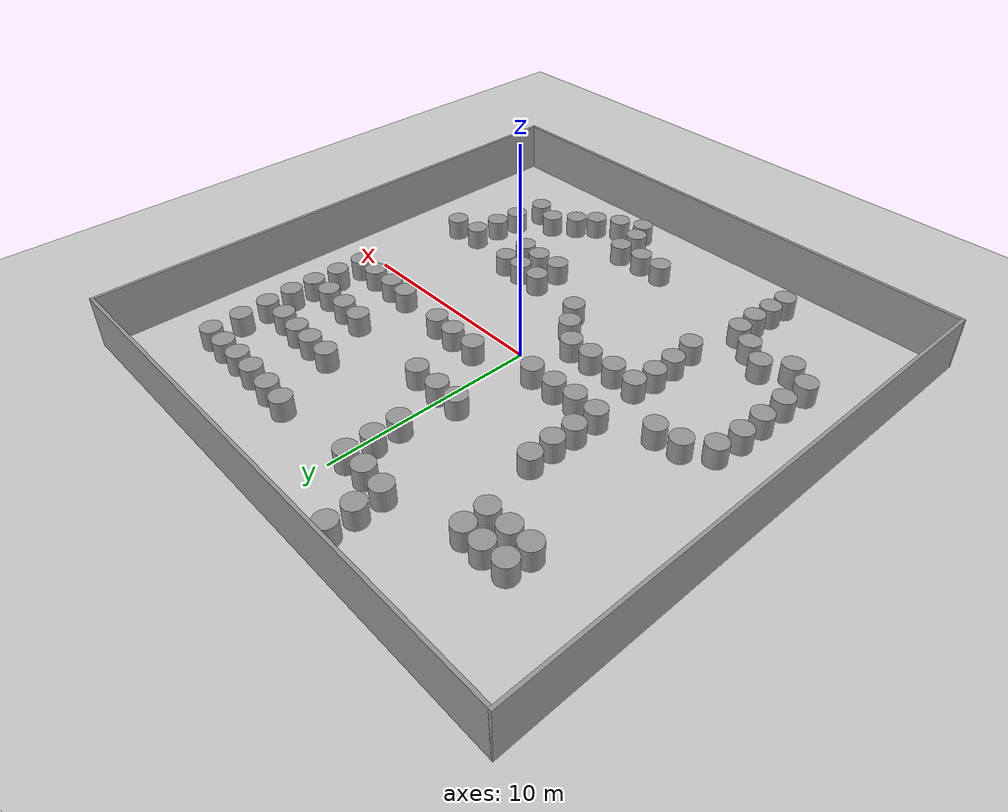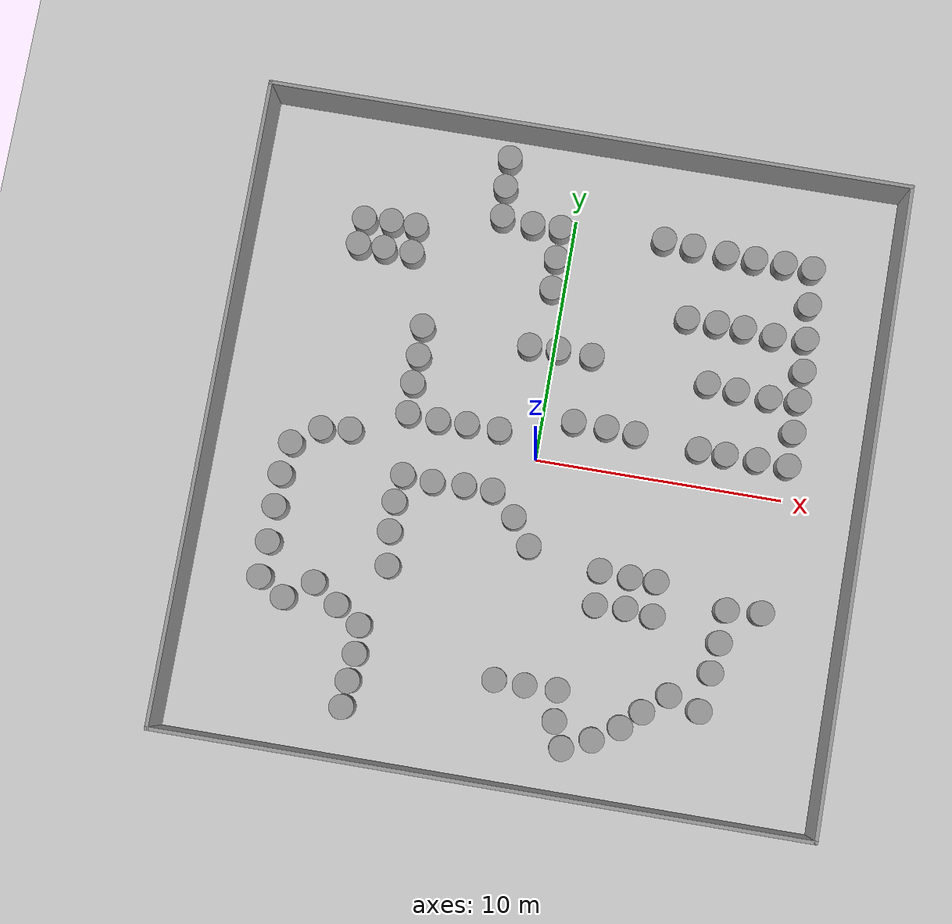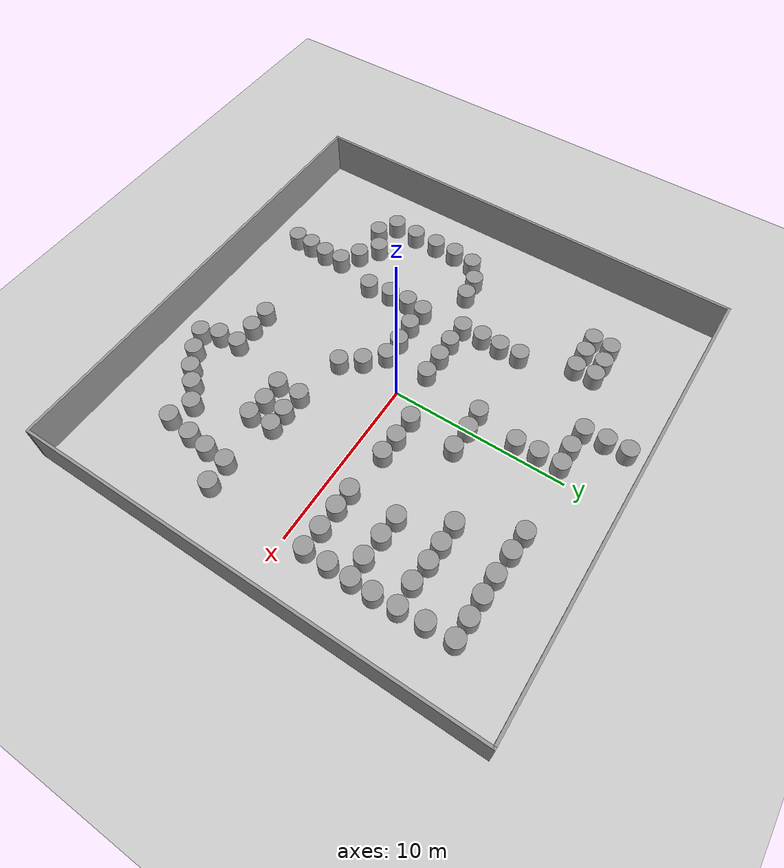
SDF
<sdf version="1.6">
 <world name="default">
  <light name="sun" type="directional">
   <pose>0 0 10 0 -0 0</pose>
   <diffuse>0.8 0.8 0.8 1</diffuse>
   <specular>0.1 0.1 0.1 1</specular>
   <attenuation>
    <range>1000</range>
    <constant>0.9</constant>
    <linear>0.01</linear>
    <quadratic>0.001</quadratic>
   </attenuation>
   <direction>-0.5 0.5 -1</direction>
  </light>
  <model name="ground_plane">
   <static>1</static>
   <link name="link">
    <collision name="collision">
     <geometry><plane><normal>0 0 1</normal><size>100 100</size></plane></geometry>
     <surface><friction><ode><mu>100</mu><mu2>50</mu2></ode></friction></surface>
    </collision>
    <visual name="visual">
     <cast_shadows>0</cast_shadows>
     <geometry><plane><normal>0 0 1</normal><size>100 100</size></plane></geometry>
     <material>
      <script><uri>file://media/materials/scripts/gazebo.material</uri><name>Gazebo/Grey</name></script>
     </material>
    </visual>
   </link>
  </model>
  <gravity>0 0 -9.8</gravity>
  <magnetic_field>6e-06 2.3e-05 -4.2e-05</magnetic_field>
  <atmosphere type="adiabatic"/>
  <physics name="default_physics" default="0" type="ode">
   <max_step_size>0.001</max_step_size>
   <real_time_factor>1</real_time_factor>
   <real_time_update_rate>1000</real_time_update_rate>
  </physics>
  <scene><ambient>0.4 0.4 0.4 1</ambient><background>0.7 0.7 0.7 1</background><shadows>1</shadows></scene>
  <spherical_coordinates>
   <surface_model>EARTH_WGS84</surface_model>
   <latitude_deg>0</latitude_deg>
   <longitude_deg>0</longitude_deg>
   <elevation>0</elevation>
   <heading_deg>0</heading_deg>
  </spherical_coordinates>
  <model name="pp_test_2">
   <link name="Wall_0">
    <collision name="Wall_0_Collision">
     <geometry><box><size>26.15 0.15 2.5</size></box></geometry>
     <pose>0 0 1.25 0 -0 0</pose>
    </collision>
    <visual name="Wall_0_Visual">
     <pose>0 0 1.25 0 -0 0</pose>
     <geometry><box><size>26.15 0.15 2.5</size></box></geometry>
     <material>
      <script><uri>file://media/materials/scripts/gazebo.material</uri><name>Gazebo/Grey</name></script>
      <ambient>1 1 1 1</ambient>
     </material>
    </visual>
    <pose>0 13 0 0 -0 0</pose>
   </link>
   <link name="Wall_2">
    <collision name="Wall_2_Collision">
     <geometry><box><size>26.15 0.15 2.5</size></box></geometry>
     <pose>0 0 1.25 0 -0 0</pose>
    </collision>
    <visual name="Wall_2_Visual">
     <pose>0 0 1.25 0 -0 0</pose>
     <geometry><box><size>26.15 0.15 2.5</size></box></geometry>
     <material>
      <script><uri>file://media/materials/scripts/gazebo.material</uri><name>Gazebo/Grey</name></script>
      <ambient>1 1 1 1</ambient>
     </material>
    </visual>
    <pose>13 0 0 0 0 -1.5708</pose>
   </link>
   <link name="Wall_4">
    <collision name="Wall_4_Collision">
     <geometry><box><size>26.15 0.15 2.5</size></box></geometry>
     <pose>0 0 1.25 0 -0 0</pose>
    </collision>
    <visual name="Wall_4_Visual">
     <pose>0 0 1.25 0 -0 0</pose>
     <geometry><box><size>26.15 0.15 2.5</size></box></geometry>
     <material>
      <script><uri>file://media/materials/scripts/gazebo.material</uri><name>Gazebo/Grey</name></script>
      <ambient>1 1 1 1</ambient>
     </material>
    </visual>
    <pose>0 -13 0 0 -0 3.14159</pose>
   </link>
   <link name="Wall_6">
    <collision name="Wall_6_Collision">
     <geometry><box><size>26.15 0.15 2.5</size></box></geometry>
     <pose>0 0 1.25 0 -0 0</pose>
    </collision>
    <visual name="Wall_6_Visual">
     <pose>0 0 1.25 0 -0 0</pose>
     <geometry><box><size>26.15 0.15 2.5</size></box></geometry>
     <material>
      <script><uri>file://media/materials/scripts/gazebo.material</uri><name>Gazebo/Grey</name></script>
      <ambient>1 1 1 1</ambient>
     </material>
    </visual>
    <pose>-13 0 0 0 -0 1.5708</pose>
   </link>
   <static>1</static>
  </model>
  <model name="unit_cylinder_0">
   <pose>-8.51606 8.48994 0.499996 2e-06 -0 0</pose>
   <link name="link">
    <inertial>
     <mass>1</mass>
     <inertia><ixx>0.145833</ixx><ixy>0</ixy><ixz>0</ixz><iyy>0.145833</iyy><iyz>0</iyz><izz>0.125</izz></inertia>
    </inertial>
    <collision name="collision">
     <geometry><cylinder><radius>0.5</radius><length>1</length></cylinder></geometry>
    </collision>
    <visual name="visual">
     <geometry><cylinder><radius>0.5</radius><length>1</length></cylinder></geometry>
     <material>
      <script><name>Gazebo/Grey</name><uri>file://media/materials/scripts/gazebo.material</uri></script>
     </material>
    </visual>
   </link>
  </model>
  <model name="unit_cylinder_1">
   <pose>-7.41702 8.57099 0.499994 -2e-06 0 0</pose>
   <link name="link">
    <inertial>
     <mass>1</mass>
     <inertia><ixx>0.145833</ixx><ixy>0</ixy><ixz>0</ixz><iyy>0.145833</iyy><iyz>0</iyz><izz>0.125</izz></inertia>
    </inertial>
    <collision name="collision">
     <geometry><cylinder><radius>0.5</radius><length>1</length></cylinder></geometry>
    </collision>
    <visual name="visual">
     <geometry><cylinder><radius>0.5</radius><length>1</length></cylinder></geometry>
     <material>
      <script><name>Gazebo/Grey</name><uri>file://media/materials/scripts/gazebo.material</uri></script>
     </material>
    </visual>
   </link>
  </model>
  <model name="unit_cylinder_2">
   <pose>-6.39638 8.54646 0.499996 2e-06 -0 0</pose>
   <link name="link">
    <inertial>
     <mass>1</mass>
     <inertia><ixx>0.145833</ixx><ixy>0</ixy><ixz>0</ixz><iyy>0.145833</iyy><iyz>0</iyz><izz>0.125</izz></inertia>
    </inertial>
    <collision name="collision">
     <geometry><cylinder><radius>0.5</radius><length>1</length></cylinder></geometry>
    </collision>
    <visual name="visual">
     <geometry><cylinder><radius>0.5</radius><length>1</length></cylinder></geometry>
     <material>
      <script><name>Gazebo/Grey</name><uri>file://media/materials/scripts/gazebo.material</uri></script>
     </material>
    </visual>
   </link>
  </model>
  <model name="unit_cylinder_3">
   <pose>-8.57488 7.4197 0.499994 -2e-06 0 0</pose>
   <link name="link">
    <inertial>
     <mass>1</mass>
     <inertia><ixx>0.145833</ixx><ixy>0</ixy><ixz>0</ixz><iyy>0.145833</iyy><iyz>0</iyz><izz>0.125</izz></inertia>
    </inertial>
    <collision name="collision">
     <geometry><cylinder><radius>0.5</radius><length>1</length></cylinder></geometry>
    </collision>
    <visual name="visual">
     <geometry><cylinder><radius>0.5</radius><length>1</length></cylinder></geometry>
     <material>
      <script><name>Gazebo/Grey</name><uri>file://media/materials/scripts/gazebo.material</uri></script>
     </material>
    </visual>
   </link>
  </model>
  <model name="unit_cylinder_3_clone">
   <pose>-7.51975 7.42894 0.499996 2e-06 -0 0</pose>
   <link name="link">
    <inertial>
     <mass>1</mass>
     <inertia><ixx>0.145833</ixx><ixy>0</ixy><ixz>0</ixz><iyy>0.145833</iyy><iyz>0</iyz><izz>0.125</izz></inertia>
    </inertial>
    <collision name="collision">
     <geometry><cylinder><radius>0.5</radius><length>1</length></cylinder></geometry>
    </collision>
    <visual name="visual">
     <geometry><cylinder><radius>0.5</radius><length>1</length></cylinder></geometry>
     <material>
      <script><name>Gazebo/Grey</name><uri>file://media/materials/scripts/gazebo.material</uri></script>
     </material>
    </visual>
   </link>
  </model>
  <model name="unit_cylinder_3_clone_0">
   <pose>-6.37172 7.42467 0.499994 -2e-06 0 0</pose>
   <link name="link">
    <inertial>
     <mass>1</mass>
     <inertia><ixx>0.145833</ixx><ixy>0</ixy><ixz>0</ixz><iyy>0.145833</iyy><iyz>0</iyz><izz>0.125</izz></inertia>
    </inertial>
    <collision name="collision">
     <geometry><cylinder><radius>0.5</radius><length>1</length></cylinder></geometry>
    </collision>
    <visual name="visual">
     <geometry><cylinder><radius>0.5</radius><length>1</length></cylinder></geometry>
     <material>
      <script><name>Gazebo/Grey</name><uri>file://media/materials/scripts/gazebo.material</uri></script>
     </material>
    </visual>
   </link>
  </model>
  <model name="unit_cylinder_3_clone_1">
   <pose>-5.41765 4.49836 0.499996 2e-06 -0 0</pose>
   <link name="link">
    <inertial>
     <mass>1</mass>
     <inertia><ixx>0.145833</ixx><ixy>0</ixy><ixz>0</ixz><iyy>0.145833</iyy><iyz>0</iyz><izz>0.125</izz></inertia>
    </inertial>
    <collision name="collision">
     <geometry><cylinder><radius>0.5</radius><length>1</length></cylinder></geometry>
    </collision>
    <visual name="visual">
     <geometry><cylinder><radius>0.5</radius><length>1</length></cylinder></geometry>
     <material>
      <script><name>Gazebo/Grey</name><uri>file://media/materials/scripts/gazebo.material</uri></script>
     </material>
    </visual>
   </link>
  </model>
  <model name="unit_cylinder_3_clone_2">
   <pose>-5.36946 3.2912 0.499994 -2e-06 -1e-06 0</pose>
   <link name="link">
    <inertial>
     <mass>1</mass>
     <inertia><ixx>0.145833</ixx><ixy>0</ixy><ixz>0</ixz><iyy>0.145833</iyy><iyz>0</iyz><izz>0.125</izz></inertia>
    </inertial>
    <collision name="collision">
     <geometry><cylinder><radius>0.5</radius><length>1</length></cylinder></geometry>
    </collision>
    <visual name="visual">
     <geometry><cylinder><radius>0.5</radius><length>1</length></cylinder></geometry>
     <material>
      <script><name>Gazebo/Grey</name><uri>file://media/materials/scripts/gazebo.material</uri></script>
     </material>
    </visual>
   </link>
  </model>
  <model name="unit_cylinder_3_clone_3">
   <pose>-5.40207 2.1536 0.499996 2e-06 1e-06 0</pose>
   <link name="link">
    <inertial>
     <mass>1</mass>
     <inertia><ixx>0.145833</ixx><ixy>0</ixy><ixz>0</ixz><iyy>0.145833</iyy><iyz>0</iyz><izz>0.125</izz></inertia>
    </inertial>
    <collision name="collision">
     <geometry><cylinder><radius>0.5</radius><length>1</length></cylinder></geometry>
    </collision>
    <visual name="visual">
     <geometry><cylinder><radius>0.5</radius><length>1</length></cylinder></geometry>
     <material>
      <script><name>Gazebo/Grey</name><uri>file://media/materials/scripts/gazebo.material</uri></script>
     </material>
    </visual>
   </link>
  </model>
  <model name="unit_cylinder_3_clone_4">
   <pose>-5.37943 0.911977 0.499994 -2e-06 -1e-06 0</pose>
   <link name="link">
    <inertial>
     <mass>1</mass>
     <inertia><ixx>0.145833</ixx><ixy>0</ixy><ixz>0</ixz><iyy>0.145833</iyy><iyz>0</iyz><izz>0.125</izz></inertia>
    </inertial>
    <collision name="collision">
     <geometry><cylinder><radius>0.5</radius><length>1</length></cylinder></geometry>
    </collision>
    <visual name="visual">
     <geometry><cylinder><radius>0.5</radius><length>1</length></cylinder></geometry>
     <material>
      <script><name>Gazebo/Grey</name><uri>file://media/materials/scripts/gazebo.material</uri></script>
     </material>
    </visual>
   </link>
  </model>
  <model name="unit_cylinder_3_clone_5">
   <pose>-4.14131 0.836526 0.499996 2e-06 1e-06 0</pose>
   <link name="link">
    <inertial>
     <mass>1</mass>
     <inertia><ixx>0.145833</ixx><ixy>0</ixy><ixz>0</ixz><iyy>0.145833</iyy><iyz>0</iyz><izz>0.125</izz></inertia>
    </inertial>
    <collision name="collision">
     <geometry><cylinder><radius>0.5</radius><length>1</length></cylinder></geometry>
    </collision>
    <visual name="visual">
     <geometry><cylinder><radius>0.5</radius><length>1</length></cylinder></geometry>
     <material>
      <script><name>Gazebo/Grey</name><uri>file://media/materials/scripts/gazebo.material</uri></script>
     </material>
    </visual>
   </link>
  </model>
  <model name="unit_cylinder_3_clone_6">
   <pose>-2.96863 0.874308 0.499994 -2e-06 -1e-06 0</pose>
   <link name="link">
    <inertial>
     <mass>1</mass>
     <inertia><ixx>0.145833</ixx><ixy>0</ixy><ixz>0</ixz><iyy>0.145833</iyy><iyz>0</iyz><izz>0.125</izz></inertia>
    </inertial>
    <collision name="collision">
     <geometry><cylinder><radius>0.5</radius><length>1</length></cylinder></geometry>
    </collision>
    <visual name="visual">
     <geometry><cylinder><radius>0.5</radius><length>1</length></cylinder></geometry>
     <material>
      <script><name>Gazebo/Grey</name><uri>file://media/materials/scripts/gazebo.material</uri></script>
     </material>
    </visual>
   </link>
  </model>
  <model name="unit_cylinder_3_clone_7">
   <pose>-1.65108 0.864726 0.499996 2e-06 1e-06 0</pose>
   <link name="link">
    <inertial>
     <mass>1</mass>
     <inertia><ixx>0.145833</ixx><ixy>0</ixy><ixz>0</ixz><iyy>0.145833</iyy><iyz>0</iyz><izz>0.125</izz></inertia>
    </inertial>
    <collision name="collision">
     <geometry><cylinder><radius>0.5</radius><length>1</length></cylinder></geometry>
    </collision>
    <visual name="visual">
     <geometry><cylinder><radius>0.5</radius><length>1</length></cylinder></geometry>
     <material>
      <script><name>Gazebo/Grey</name><uri>file://media/materials/scripts/gazebo.material</uri></script>
     </material>
    </visual>
   </link>
  </model>
  <model name="unit_cylinder_3_clone_8">
   <pose>-1.49686 -1.59938 0.499994 -2e-06 -1e-06 0</pose>
   <link name="link">
    <inertial>
     <mass>1</mass>
     <inertia><ixx>0.145833</ixx><ixy>0</ixy><ixz>0</ixz><iyy>0.145833</iyy><iyz>0</iyz><izz>0.125</izz></inertia>
    </inertial>
    <collision name="collision">
     <geometry><cylinder><radius>0.5</radius><length>1</length></cylinder></geometry>
    </collision>
    <visual name="visual">
     <geometry><cylinder><radius>0.5</radius><length>1</length></cylinder></geometry>
     <material>
      <script><name>Gazebo/Grey</name><uri>file://media/materials/scripts/gazebo.material</uri></script>
     </material>
    </visual>
   </link>
  </model>
  <model name="unit_cylinder_3_clone_9">
   <pose>-2.65788 -1.58084 0.499996 2e-06 1e-06 0</pose>
   <link name="link">
    <inertial>
     <mass>1</mass>
     <inertia><ixx>0.145833</ixx><ixy>0</ixy><ixz>0</ixz><iyy>0.145833</iyy><iyz>0</iyz><izz>0.125</izz></inertia>
    </inertial>
    <collision name="collision">
     <geometry><cylinder><radius>0.5</radius><length>1</length></cylinder></geometry>
    </collision>
    <visual name="visual">
     <geometry><cylinder><radius>0.5</radius><length>1</length></cylinder></geometry>
     <material>
      <script><name>Gazebo/Grey</name><uri>file://media/materials/scripts/gazebo.material</uri></script>
     </material>
    </visual>
   </link>
  </model>
  <model name="unit_cylinder_3_clone_10">
   <pose>-3.93267 -1.65023 0.499994 -2e-06 -1e-06 0</pose>
   <link name="link">
    <inertial>
     <mass>1</mass>
     <inertia><ixx>0.145833</ixx><ixy>0</ixy><ixz>0</ixz><iyy>0.145833</iyy><iyz>0</iyz><izz>0.125</izz></inertia>
    </inertial>
    <collision name="collision">
     <geometry><cylinder><radius>0.5</radius><length>1</length></cylinder></geometry>
    </collision>
    <visual name="visual">
     <geometry><cylinder><radius>0.5</radius><length>1</length></cylinder></geometry>
     <material>
      <script><name>Gazebo/Grey</name><uri>file://media/materials/scripts/gazebo.material</uri></script>
     </material>
    </visual>
   </link>
  </model>
  <model name="unit_cylinder_3_clone_11">
   <pose>-5.14336 -1.57667 0.499996 3e-06 1e-06 -0</pose>
   <link name="link">
    <inertial>
     <mass>1</mass>
     <inertia><ixx>0.145833</ixx><ixy>0</ixy><ixz>0</ixz><iyy>0.145833</iyy><iyz>0</iyz><izz>0.125</izz></inertia>
    </inertial>
    <collision name="collision">
     <geometry><cylinder><radius>0.5</radius><length>1</length></cylinder></geometry>
    </collision>
    <visual name="visual">
     <geometry><cylinder><radius>0.5</radius><length>1</length></cylinder></geometry>
     <material>
      <script><name>Gazebo/Grey</name><uri>file://media/materials/scripts/gazebo.material</uri></script>
     </material>
    </visual>
   </link>
  </model>
  <model name="unit_cylinder_3_clone_12">
   <pose>-5.289 -2.68054 0.499994 -3e-06 -1e-06 -0</pose>
   <link name="link">
    <inertial>
     <mass>1</mass>
     <inertia><ixx>0.145833</ixx><ixy>0</ixy><ixz>0</ixz><iyy>0.145833</iyy><iyz>0</iyz><izz>0.125</izz></inertia>
    </inertial>
    <collision name="collision">
     <geometry><cylinder><radius>0.5</radius><length>1</length></cylinder></geometry>
    </collision>
    <visual name="visual">
     <geometry><cylinder><radius>0.5</radius><length>1</length></cylinder></geometry>
     <material>
      <script><name>Gazebo/Grey</name><uri>file://media/materials/scripts/gazebo.material</uri></script>
     </material>
    </visual>
   </link>
  </model>
  <model name="unit_cylinder_3_clone_13">
   <pose>-5.26765 -3.88171 0.499996 3e-06 1e-06 -0</pose>
   <link name="link">
    <inertial>
     <mass>1</mass>
     <inertia><ixx>0.145833</ixx><ixy>0</ixy><ixz>0</ixz><iyy>0.145833</iyy><iyz>0</iyz><izz>0.125</izz></inertia>
    </inertial>
    <collision name="collision">
     <geometry><cylinder><radius>0.5</radius><length>1</length></cylinder></geometry>
    </collision>
    <visual name="visual">
     <geometry><cylinder><radius>0.5</radius><length>1</length></cylinder></geometry>
     <material>
      <script><name>Gazebo/Grey</name><uri>file://media/materials/scripts/gazebo.material</uri></script>
     </material>
    </visual>
   </link>
  </model>
  <model name="unit_cylinder_3_clone_14">
   <pose>-5.10953 -5.24772 0.499994 -3e-06 -1e-06 -0</pose>
   <link name="link">
    <inertial>
     <mass>1</mass>
     <inertia><ixx>0.145833</ixx><ixy>0</ixy><ixz>0</ixz><iyy>0.145833</iyy><iyz>0</iyz><izz>0.125</izz></inertia>
    </inertial>
    <collision name="collision">
     <geometry><cylinder><radius>0.5</radius><length>1</length></cylinder></geometry>
    </collision>
    <visual name="visual">
     <geometry><cylinder><radius>0.5</radius><length>1</length></cylinder></geometry>
     <material>
      <script><name>Gazebo/Grey</name><uri>file://media/materials/scripts/gazebo.material</uri></script>
     </material>
    </visual>
   </link>
  </model>
  <model name="unit_cylinder_3_clone_15">
   <pose>-0.485963 -2.51006 0.499996 3e-06 1e-06 -0</pose>
   <link name="link">
    <inertial>
     <mass>1</mass>
     <inertia><ixx>0.145833</ixx><ixy>0</ixy><ixz>0</ixz><iyy>0.145833</iyy><iyz>0</iyz><izz>0.125</izz></inertia>
    </inertial>
    <collision name="collision">
     <geometry><cylinder><radius>0.5</radius><length>1</length></cylinder></geometry>
    </collision>
    <visual name="visual">
     <geometry><cylinder><radius>0.5</radius><length>1</length></cylinder></geometry>
     <material>
      <script><name>Gazebo/Grey</name><uri>file://media/materials/scripts/gazebo.material</uri></script>
     </material>
    </visual>
   </link>
  </model>
  <model name="unit_cylinder_3_clone_16">
   <pose>0.297227 -3.55585 0.499994 -3e-06 -1e-06 -0</pose>
   <link name="link">
    <inertial>
     <mass>1</mass>
     <inertia><ixx>0.145833</ixx><ixy>0</ixy><ixz>0</ixz><iyy>0.145833</iyy><iyz>0</iyz><izz>0.125</izz></inertia>
    </inertial>
    <collision name="collision">
     <geometry><cylinder><radius>0.5</radius><length>1</length></cylinder></geometry>
    </collision>
    <visual name="visual">
     <geometry><cylinder><radius>0.5</radius><length>1</length></cylinder></geometry>
     <material>
      <script><name>Gazebo/Grey</name><uri>file://media/materials/scripts/gazebo.material</uri></script>
     </material>
    </visual>
   </link>
  </model>
  <model name="unit_cylinder_3_clone_17">
   <pose>-1.02332 4.44056 0.499996 3e-06 1e-06 -0</pose>
   <link name="link">
    <inertial>
     <mass>1</mass>
     <inertia><ixx>0.145833</ixx><ixy>0</ixy><ixz>0</ixz><iyy>0.145833</iyy><iyz>0</iyz><izz>0.125</izz></inertia>
    </inertial>
    <collision name="collision">
     <geometry><cylinder><radius>0.5</radius><length>1</length></cylinder></geometry>
    </collision>
    <visual name="visual">
     <geometry><cylinder><radius>0.5</radius><length>1</length></cylinder></geometry>
     <material>
      <script><name>Gazebo/Grey</name><uri>file://media/materials/scripts/gazebo.material</uri></script>
     </material>
    </visual>
   </link>
  </model>
  <model name="unit_cylinder_3_clone_18">
   <pose>0.150944 4.48466 0.499994 -3e-06 -1e-06 -0</pose>
   <link name="link">
    <inertial>
     <mass>1</mass>
     <inertia><ixx>0.145833</ixx><ixy>0</ixy><ixz>0</ixz><iyy>0.145833</iyy><iyz>0</iyz><izz>0.125</izz></inertia>
    </inertial>
    <collision name="collision">
     <geometry><cylinder><radius>0.5</radius><length>1</length></cylinder></geometry>
    </collision>
    <visual name="visual">
     <geometry><cylinder><radius>0.5</radius><length>1</length></cylinder></geometry>
     <material>
      <script><name>Gazebo/Grey</name><uri>file://media/materials/scripts/gazebo.material</uri></script>
     </material>
    </visual>
   </link>
  </model>
  <model name="unit_cylinder_3_clone_19">
   <pose>1.52572 4.44658 0.499996 3e-06 1e-06 -0</pose>
   <link name="link">
    <inertial>
     <mass>1</mass>
     <inertia><ixx>0.145833</ixx><ixy>0</ixy><ixz>0</ixz><iyy>0.145833</iyy><iyz>0</iyz><izz>0.125</izz></inertia>
    </inertial>
    <collision name="collision">
     <geometry><cylinder><radius>0.5</radius><length>1</length></cylinder></geometry>
    </collision>
    <visual name="visual">
     <geometry><cylinder><radius>0.5</radius><length>1</length></cylinder></geometry>
     <material>
      <script><name>Gazebo/Grey</name><uri>file://media/materials/scripts/gazebo.material</uri></script>
     </material>
    </visual>
   </link>
  </model>
  <model name="unit_cylinder_3_clone_20">
   <pose>3.64653 9.65426 0.499994 -3e-06 -1e-06 -0</pose>
   <link name="link">
    <inertial>
     <mass>1</mass>
     <inertia><ixx>0.145833</ixx><ixy>0</ixy><ixz>0</ixz><iyy>0.145833</iyy><iyz>0</iyz><izz>0.125</izz></inertia>
    </inertial>
    <collision name="collision">
     <geometry><cylinder><radius>0.5</radius><length>1</length></cylinder></geometry>
    </collision>
    <visual name="visual">
     <geometry><cylinder><radius>0.5</radius><length>1</length></cylinder></geometry>
     <material>
      <script><name>Gazebo/Grey</name><uri>file://media/materials/scripts/gazebo.material</uri></script>
     </material>
    </visual>
   </link>
  </model>
  <model name="unit_cylinder_3_clone_21">
   <pose>4.85553 9.57337 0.499996 3e-06 1e-06 -0</pose>
   <link name="link">
    <inertial>
     <mass>1</mass>
     <inertia><ixx>0.145833</ixx><ixy>0</ixy><ixz>0</ixz><iyy>0.145833</iyy><iyz>0</iyz><izz>0.125</izz></inertia>
    </inertial>
    <collision name="collision">
     <geometry><cylinder><radius>0.5</radius><length>1</length></cylinder></geometry>
    </collision>
    <visual name="visual">
     <geometry><cylinder><radius>0.5</radius><length>1</length></cylinder></geometry>
     <material>
      <script><name>Gazebo/Grey</name><uri>file://media/materials/scripts/gazebo.material</uri></script>
     </material>
    </visual>
   </link>
  </model>
  <model name="unit_cylinder_3_clone_22">
   <pose>6.2344 9.50314 0.499994 -3e-06 -1e-06 -0</pose>
   <link name="link">
    <inertial>
     <mass>1</mass>
     <inertia><ixx>0.145833</ixx><ixy>0</ixy><ixz>0</ixz><iyy>0.145833</iyy><iyz>0</iyz><izz>0.125</izz></inertia>
    </inertial>
    <collision name="collision">
     <geometry><cylinder><radius>0.5</radius><length>1</length></cylinder></geometry>
    </collision>
    <visual name="visual">
     <geometry><cylinder><radius>0.5</radius><length>1</length></cylinder></geometry>
     <material>
      <script><name>Gazebo/Grey</name><uri>file://media/materials/scripts/gazebo.material</uri></script>
     </material>
    </visual>
   </link>
  </model>
  <model name="unit_cylinder_3_clone_23">
   <pose>7.41881 9.47437 0.499996 3e-06 1e-06 -0</pose>
   <link name="link">
    <inertial>
     <mass>1</mass>
     <inertia><ixx>0.145833</ixx><ixy>0</ixy><ixz>0</ixz><iyy>0.145833</iyy><iyz>0</iyz><izz>0.125</izz></inertia>
    </inertial>
    <collision name="collision">
     <geometry><cylinder><radius>0.5</radius><length>1</length></cylinder></geometry>
    </collision>
    <visual name="visual">
     <geometry><cylinder><radius>0.5</radius><length>1</length></cylinder></geometry>
     <material>
      <script><name>Gazebo/Grey</name><uri>file://media/materials/scripts/gazebo.material</uri></script>
     </material>
    </visual>
   </link>
  </model>
  <model name="unit_cylinder_3_clone_24">
   <pose>8.621 9.4767 0.499994 -3e-06 -1e-06 -0</pose>
   <link name="link">
    <inertial>
     <mass>1</mass>
     <inertia><ixx>0.145833</ixx><ixy>0</ixy><ixz>0</ixz><iyy>0.145833</iyy><iyz>0</iyz><izz>0.125</izz></inertia>
    </inertial>
    <collision name="collision">
     <geometry><cylinder><radius>0.5</radius><length>1</length></cylinder></geometry>
    </collision>
    <visual name="visual">
     <geometry><cylinder><radius>0.5</radius><length>1</length></cylinder></geometry>
     <material>
      <script><name>Gazebo/Grey</name><uri>file://media/materials/scripts/gazebo.material</uri></script>
     </material>
    </visual>
   </link>
  </model>
  <model name="unit_cylinder_3_clone_25">
   <pose>9.77818 9.44871 0.499996 3e-06 1e-06 -0</pose>
   <link name="link">
    <inertial>
     <mass>1</mass>
     <inertia><ixx>0.145833</ixx><ixy>0</ixy><ixz>0</ixz><iyy>0.145833</iyy><iyz>0</iyz><izz>0.125</izz></inertia>
    </inertial>
    <collision name="collision">
     <geometry><cylinder><radius>0.5</radius><length>1</length></cylinder></geometry>
    </collision>
    <visual name="visual">
     <geometry><cylinder><radius>0.5</radius><length>1</length></cylinder></geometry>
     <material>
      <script><name>Gazebo/Grey</name><uri>file://media/materials/scripts/gazebo.material</uri></script>
     </material>
    </visual>
   </link>
  </model>
  <model name="unit_cylinder_3_clone_26">
   <pose>9.84593 7.94617 0.499994 -3e-06 -1e-06 -0</pose>
   <link name="link">
    <inertial>
     <mass>1</mass>
     <inertia><ixx>0.145833</ixx><ixy>0</ixy><ixz>0</ixz><iyy>0.145833</iyy><iyz>0</iyz><izz>0.125</izz></inertia>
    </inertial>
    <collision name="collision">
     <geometry><cylinder><radius>0.5</radius><length>1</length></cylinder></geometry>
    </collision>
    <visual name="visual">
     <geometry><cylinder><radius>0.5</radius><length>1</length></cylinder></geometry>
     <material>
      <script><name>Gazebo/Grey</name><uri>file://media/materials/scripts/gazebo.material</uri></script>
     </material>
    </visual>
   </link>
  </model>
  <model name="unit_cylinder_3_clone_27">
   <pose>9.947 6.53993 0.499996 3e-06 1e-06 -0</pose>
   <link name="link">
    <inertial>
     <mass>1</mass>
     <inertia><ixx>0.145833</ixx><ixy>0</ixy><ixz>0</ixz><iyy>0.145833</iyy><iyz>0</iyz><izz>0.125</izz></inertia>
    </inertial>
    <collision name="collision">
     <geometry><cylinder><radius>0.5</radius><length>1</length></cylinder></geometry>
    </collision>
    <visual name="visual">
     <geometry><cylinder><radius>0.5</radius><length>1</length></cylinder></geometry>
     <material>
      <script><name>Gazebo/Grey</name><uri>file://media/materials/scripts/gazebo.material</uri></script>
     </material>
    </visual>
   </link>
  </model>
  <model name="unit_cylinder_3_clone_28">
   <pose>8.62726 6.4657 0.499996 3e-06 1e-06 -0</pose>
   <link name="link">
    <inertial>
     <mass>1</mass>
     <inertia><ixx>0.145833</ixx><ixy>0</ixy><ixz>0</ixz><iyy>0.145833</iyy><iyz>0</iyz><izz>0.125</izz></inertia>
    </inertial>
    <collision name="collision">
     <geometry><cylinder><radius>0.5</radius><length>1</length></cylinder></geometry>
    </collision>
    <visual name="visual">
     <geometry><cylinder><radius>0.5</radius><length>1</length></cylinder></geometry>
     <material>
      <script><name>Gazebo/Grey</name><uri>file://media/materials/scripts/gazebo.material</uri></script>
     </material>
    </visual>
   </link>
  </model>
  <model name="unit_cylinder_3_clone_29">
   <pose>7.39694 6.57753 0.499996 3e-06 1e-06 -0</pose>
   <link name="link">
    <inertial>
     <mass>1</mass>
     <inertia><ixx>0.145833</ixx><ixy>0</ixy><ixz>0</ixz><iyy>0.145833</iyy><iyz>0</iyz><izz>0.125</izz></inertia>
    </inertial>
    <collision name="collision">
     <geometry><cylinder><radius>0.5</radius><length>1</length></cylinder></geometry>
    </collision>
    <visual name="visual">
     <geometry><cylinder><radius>0.5</radius><length>1</length></cylinder></geometry>
     <material>
      <script><name>Gazebo/Grey</name><uri>file://media/materials/scripts/gazebo.material</uri></script>
     </material>
    </visual>
   </link>
  </model>
  <model name="unit_cylinder_3_clone_30">
   <pose>6.29583 6.60404 0.499994 -3e-06 -1e-06 -0</pose>
   <link name="link">
    <inertial>
     <mass>1</mass>
     <inertia><ixx>0.145833</ixx><ixy>0</ixy><ixz>0</ixz><iyy>0.145833</iyy><iyz>0</iyz><izz>0.125</izz></inertia>
    </inertial>
    <collision name="collision">
     <geometry><cylinder><radius>0.5</radius><length>1</length></cylinder></geometry>
    </collision>
    <visual name="visual">
     <geometry><cylinder><radius>0.5</radius><length>1</length></cylinder></geometry>
     <material>
      <script><name>Gazebo/Grey</name><uri>file://media/materials/scripts/gazebo.material</uri></script>
     </material>
    </visual>
   </link>
  </model>
  <model name="unit_cylinder_3_clone_31">
   <pose>5.08248 6.60278 0.499994 -3e-06 -1e-06 -0</pose>
   <link name="link">
    <inertial>
     <mass>1</mass>
     <inertia><ixx>0.145833</ixx><ixy>0</ixy><ixz>0</ixz><iyy>0.145833</iyy><iyz>0</iyz><izz>0.125</izz></inertia>
    </inertial>
    <collision name="collision">
     <geometry><cylinder><radius>0.5</radius><length>1</length></cylinder></geometry>
    </collision>
    <visual name="visual">
     <geometry><cylinder><radius>0.5</radius><length>1</length></cylinder></geometry>
     <material>
      <script><name>Gazebo/Grey</name><uri>file://media/materials/scripts/gazebo.material</uri></script>
     </material>
    </visual>
   </link>
  </model>
  <model name="unit_cylinder_3_clone_32">
   <pose>10.0259 5.2307 0.499994 -3e-06 -1e-06 -0</pose>
   <link name="link">
    <inertial>
     <mass>1</mass>
     <inertia><ixx>0.145833</ixx><ixy>0</ixy><ixz>0</ixz><iyy>0.145833</iyy><iyz>0</iyz><izz>0.125</izz></inertia>
    </inertial>
    <collision name="collision">
     <geometry><cylinder><radius>0.5</radius><length>1</length></cylinder></geometry>
    </collision>
    <visual name="visual">
     <geometry><cylinder><radius>0.5</radius><length>1</length></cylinder></geometry>
     <material>
      <script><name>Gazebo/Grey</name><uri>file://media/materials/scripts/gazebo.material</uri></script>
     </material>
    </visual>
   </link>
  </model>
  <model name="unit_cylinder_3_clone_33">
   <pose>10.016 4.01311 0.499996 3e-06 1e-06 -0</pose>
   <link name="link">
    <inertial>
     <mass>1</mass>
     <inertia><ixx>0.145833</ixx><ixy>0</ixy><ixz>0</ixz><iyy>0.145833</iyy><iyz>0</iyz><izz>0.125</izz></inertia>
    </inertial>
    <collision name="collision">
     <geometry><cylinder><radius>0.5</radius><length>1</length></cylinder></geometry>
    </collision>
    <visual name="visual">
     <geometry><cylinder><radius>0.5</radius><length>1</length></cylinder></geometry>
     <material>
      <script><name>Gazebo/Grey</name><uri>file://media/materials/scripts/gazebo.material</uri></script>
     </material>
    </visual>
   </link>
  </model>
  <model name="unit_cylinder_3_clone_34">
   <pose>8.84533 3.9381 0.499996 3e-06 1e-06 -0</pose>
   <link name="link">
    <inertial>
     <mass>1</mass>
     <inertia><ixx>0.145833</ixx><ixy>0</ixy><ixz>0</ixz><iyy>0.145833</iyy><iyz>0</iyz><izz>0.125</izz></inertia>
    </inertial>
    <collision name="collision">
     <geometry><cylinder><radius>0.5</radius><length>1</length></cylinder></geometry>
    </collision>
    <visual name="visual">
     <geometry><cylinder><radius>0.5</radius><length>1</length></cylinder></geometry>
     <material>
      <script><name>Gazebo/Grey</name><uri>file://media/materials/scripts/gazebo.material</uri></script>
     </material>
    </visual>
   </link>
  </model>
  <model name="unit_cylinder_3_clone_35">
   <pose>7.50389 4.0209 0.499994 -3e-06 -1e-06 -0</pose>
   <link name="link">
    <inertial>
     <mass>1</mass>
     <inertia><ixx>0.145833</ixx><ixy>0</ixy><ixz>0</ixz><iyy>0.145833</iyy><iyz>0</iyz><izz>0.125</izz></inertia>
    </inertial>
    <collision name="collision">
     <geometry><cylinder><radius>0.5</radius><length>1</length></cylinder></geometry>
    </collision>
    <visual name="visual">
     <geometry><cylinder><radius>0.5</radius><length>1</length></cylinder></geometry>
     <material>
      <script><name>Gazebo/Grey</name><uri>file://media/materials/scripts/gazebo.material</uri></script>
     </material>
    </visual>
   </link>
  </model>
  <model name="unit_cylinder_3_clone_36">
   <pose>6.30939 4.09724 0.499994 -3e-06 -1e-06 -0</pose>
   <link name="link">
    <inertial>
     <mass>1</mass>
     <inertia><ixx>0.145833</ixx><ixy>0</ixy><ixz>0</ixz><iyy>0.145833</iyy><iyz>0</iyz><izz>0.125</izz></inertia>
    </inertial>
    <collision name="collision">
     <geometry><cylinder><radius>0.5</radius><length>1</length></cylinder></geometry>
    </collision>
    <visual name="visual">
     <geometry><cylinder><radius>0.5</radius><length>1</length></cylinder></geometry>
     <material>
      <script><name>Gazebo/Grey</name><uri>file://media/materials/scripts/gazebo.material</uri></script>
     </material>
    </visual>
   </link>
  </model>
  <model name="unit_cylinder_3_clone_37">
   <pose>9.99266 2.70377 0.499996 3e-06 1e-06 -0</pose>
   <link name="link">
    <inertial>
     <mass>1</mass>
     <inertia><ixx>0.145833</ixx><ixy>0</ixy><ixz>0</ixz><iyy>0.145833</iyy><iyz>0</iyz><izz>0.125</izz></inertia>
    </inertial>
    <collision name="collision">
     <geometry><cylinder><radius>0.5</radius><length>1</length></cylinder></geometry>
    </collision>
    <visual name="visual">
     <geometry><cylinder><radius>0.5</radius><length>1</length></cylinder></geometry>
     <material>
      <script><name>Gazebo/Grey</name><uri>file://media/materials/scripts/gazebo.material</uri></script>
     </material>
    </visual>
   </link>
  </model>
  <model name="unit_cylinder_3_clone_38">
   <pose>9.99719 1.33401 0.499996 3e-06 1e-06 -0</pose>
   <link name="link">
    <inertial>
     <mass>1</mass>
     <inertia><ixx>0.145833</ixx><ixy>0</ixy><ixz>0</ixz><iyy>0.145833</iyy><iyz>0</iyz><izz>0.125</izz></inertia>
    </inertial>
    <collision name="collision">
     <geometry><cylinder><radius>0.5</radius><length>1</length></cylinder></geometry>
    </collision>
    <visual name="visual">
     <geometry><cylinder><radius>0.5</radius><length>1</length></cylinder></geometry>
     <material>
      <script><name>Gazebo/Grey</name><uri>file://media/materials/scripts/gazebo.material</uri></script>
     </material>
    </visual>
   </link>
  </model>
  <model name="unit_cylinder_3_clone_39">
   <pose>8.7472 1.36951 0.499996 3e-06 1e-06 -0</pose>
   <link name="link">
    <inertial>
     <mass>1</mass>
     <inertia><ixx>0.145833</ixx><ixy>0</ixy><ixz>0</ixz><iyy>0.145833</iyy><iyz>0</iyz><izz>0.125</izz></inertia>
    </inertial>
    <collision name="collision">
     <geometry><cylinder><radius>0.5</radius><length>1</length></cylinder></geometry>
    </collision>
    <visual name="visual">
     <geometry><cylinder><radius>0.5</radius><length>1</length></cylinder></geometry>
     <material>
      <script><name>Gazebo/Grey</name><uri>file://media/materials/scripts/gazebo.material</uri></script>
     </material>
    </visual>
   </link>
  </model>
  <model name="unit_cylinder_3_clone_40">
   <pose>7.45409 1.37607 0.499994 -3e-06 -1e-06 -0</pose>
   <link name="link">
    <inertial>
     <mass>1</mass>
     <inertia><ixx>0.145833</ixx><ixy>0</ixy><ixz>0</ixz><iyy>0.145833</iyy><iyz>0</iyz><izz>0.125</izz></inertia>
    </inertial>
    <collision name="collision">
     <geometry><cylinder><radius>0.5</radius><length>1</length></cylinder></geometry>
    </collision>
    <visual name="visual">
     <geometry><cylinder><radius>0.5</radius><length>1</length></cylinder></geometry>
     <material>
      <script><name>Gazebo/Grey</name><uri>file://media/materials/scripts/gazebo.material</uri></script>
     </material>
    </visual>
   </link>
  </model>
  <model name="unit_cylinder_3_clone_41">
   <pose>6.36195 1.40392 0.499994 -3e-06 -1e-06 -0</pose>
   <link name="link">
    <inertial>
     <mass>1</mass>
     <inertia><ixx>0.145833</ixx><ixy>0</ixy><ixz>0</ixz><iyy>0.145833</iyy><iyz>0</iyz><izz>0.125</izz></inertia>
    </inertial>
    <collision name="collision">
     <geometry><cylinder><radius>0.5</radius><length>1</length></cylinder></geometry>
    </collision>
    <visual name="visual">
     <geometry><cylinder><radius>0.5</radius><length>1</length></cylinder></geometry>
     <material>
      <script><name>Gazebo/Grey</name><uri>file://media/materials/scripts/gazebo.material</uri></script>
     </material>
    </visual>
   </link>
  </model>
  <model name="unit_cylinder_3_clone_42">
   <pose>1.24006 1.67277 0.499994 -3e-06 -1e-06 -0</pose>
   <link name="link">
    <inertial>
     <mass>1</mass>
     <inertia><ixx>0.145833</ixx><ixy>0</ixy><ixz>0</ixz><iyy>0.145833</iyy><iyz>0</iyz><izz>0.125</izz></inertia>
    </inertial>
    <collision name="collision">
     <geometry><cylinder><radius>0.5</radius><length>1</length></cylinder></geometry>
    </collision>
    <visual name="visual">
     <geometry><cylinder><radius>0.5</radius><length>1</length></cylinder></geometry>
     <material>
      <script><name>Gazebo/Grey</name><uri>file://media/materials/scripts/gazebo.material</uri></script>
     </material>
    </visual>
   </link>
  </model>
  <model name="unit_cylinder_3_clone_43">
   <pose>2.58391 1.66549 0.499994 -3e-06 -1e-06 -0</pose>
   <link name="link">
    <inertial>
     <mass>1</mass>
     <inertia><ixx>0.145833</ixx><ixy>0</ixy><ixz>0</ixz><iyy>0.145833</iyy><iyz>0</iyz><izz>0.125</izz></inertia>
    </inertial>
    <collision name="collision">
     <geometry><cylinder><radius>0.5</radius><length>1</length></cylinder></geometry>
    </collision>
    <visual name="visual">
     <geometry><cylinder><radius>0.5</radius><length>1</length></cylinder></geometry>
     <material>
      <script><name>Gazebo/Grey</name><uri>file://media/materials/scripts/gazebo.material</uri></script>
     </material>
    </visual>
   </link>
  </model>
  <model name="unit_cylinder_3_clone_44">
   <pose>3.76672 1.6047 0.499997 3e-06 2e-06 0</pose>
   <link name="link">
    <inertial>
     <mass>1</mass>
     <inertia><ixx>0.145833</ixx><ixy>0</ixy><ixz>0</ixz><iyy>0.145833</iyy><iyz>0</iyz><izz>0.125</izz></inertia>
    </inertial>
    <collision name="collision">
     <geometry><cylinder><radius>0.5</radius><length>1</length></cylinder></geometry>
    </collision>
    <visual name="visual">
     <geometry><cylinder><radius>0.5</radius><length>1</length></cylinder></geometry>
     <material>
      <script><name>Gazebo/Grey</name><uri>file://media/materials/scripts/gazebo.material</uri></script>
     </material>
    </visual>
   </link>
  </model>
  <model name="unit_cylinder_3_clone_45">
   <pose>-9.79398 -1.03139 0.499997 3e-06 2e-06 0</pose>
   <link name="link">
    <inertial>
     <mass>1</mass>
     <inertia><ixx>0.145833</ixx><ixy>0</ixy><ixz>0</ixz><iyy>0.145833</iyy><iyz>0</iyz><izz>0.125</izz></inertia>
    </inertial>
    <collision name="collision">
     <geometry><cylinder><radius>0.5</radius><length>1</length></cylinder></geometry>
    </collision>
    <visual name="visual">
     <geometry><cylinder><radius>0.5</radius><length>1</length></cylinder></geometry>
     <material>
      <script><name>Gazebo/Grey</name><uri>file://media/materials/scripts/gazebo.material</uri></script>
     </material>
    </visual>
   </link>
  </model>
  <model name="unit_cylinder_3_clone_46">
   <pose>-8.70421 -0.26571 0.499997 3e-06 2e-06 0</pose>
   <link name="link">
    <inertial>
     <mass>1</mass>
     <inertia><ixx>0.145833</ixx><ixy>0</ixy><ixz>0</ixz><iyy>0.145833</iyy><iyz>0</iyz><izz>0.125</izz></inertia>
    </inertial>
    <collision name="collision">
     <geometry><cylinder><radius>0.5</radius><length>1</length></cylinder></geometry>
    </collision>
    <visual name="visual">
     <geometry><cylinder><radius>0.5</radius><length>1</length></cylinder></geometry>
     <material>
      <script><name>Gazebo/Grey</name><uri>file://media/materials/scripts/gazebo.material</uri></script>
     </material>
    </visual>
   </link>
  </model>
  <model name="unit_cylinder_3_clone_47">
   <pose>-7.53872 -0.117283 0.499994 -3e-06 -2e-06 0</pose>
   <link name="link">
    <inertial>
     <mass>1</mass>
     <inertia><ixx>0.145833</ixx><ixy>0</ixy><ixz>0</ixz><iyy>0.145833</iyy><iyz>0</iyz><izz>0.125</izz></inertia>
    </inertial>
    <collision name="collision">
     <geometry><cylinder><radius>0.5</radius><length>1</length></cylinder></geometry>
    </collision>
    <visual name="visual">
     <geometry><cylinder><radius>0.5</radius><length>1</length></cylinder></geometry>
     <material>
      <script><name>Gazebo/Grey</name><uri>file://media/materials/scripts/gazebo.material</uri></script>
     </material>
    </visual>
   </link>
  </model>
  <model name="unit_cylinder_3_clone_48">
   <pose>-9.97561 -2.34091 0.499997 3e-06 2e-06 0</pose>
   <link name="link">
    <inertial>
     <mass>1</mass>
     <inertia><ixx>0.145833</ixx><ixy>0</ixy><ixz>0</ixz><iyy>0.145833</iyy><iyz>0</iyz><izz>0.125</izz></inertia>
    </inertial>
    <collision name="collision">
     <geometry><cylinder><radius>0.5</radius><length>1</length></cylinder></geometry>
    </collision>
    <visual name="visual">
     <geometry><cylinder><radius>0.5</radius><length>1</length></cylinder></geometry>
     <material>
      <script><name>Gazebo/Grey</name><uri>file://media/materials/scripts/gazebo.material</uri></script>
     </material>
    </visual>
   </link>
  </model>
  <model name="unit_cylinder_3_clone_49">
   <pose>-9.97675 -3.65167 0.499997 3e-06 2e-06 0</pose>
   <link name="link">
    <inertial>
     <mass>1</mass>
     <inertia><ixx>0.145833</ixx><ixy>0</ixy><ixz>0</ixz><iyy>0.145833</iyy><iyz>0</iyz><izz>0.125</izz></inertia>
    </inertial>
    <collision name="collision">
     <geometry><cylinder><radius>0.5</radius><length>1</length></cylinder></geometry>
    </collision>
    <visual name="visual">
     <geometry><cylinder><radius>0.5</radius><length>1</length></cylinder></geometry>
     <material>
      <script><name>Gazebo/Grey</name><uri>file://media/materials/scripts/gazebo.material</uri></script>
     </material>
    </visual>
   </link>
  </model>
  <model name="unit_cylinder_3_clone_50">
   <pose>-9.96936 -5.08345 0.499994 -3e-06 -2e-06 0</pose>
   <link name="link">
    <inertial>
     <mass>1</mass>
     <inertia><ixx>0.145833</ixx><ixy>0</ixy><ixz>0</ixz><iyy>0.145833</iyy><iyz>0</iyz><izz>0.125</izz></inertia>
    </inertial>
    <collision name="collision">
     <geometry><cylinder><radius>0.5</radius><length>1</length></cylinder></geometry>
    </collision>
    <visual name="visual">
     <geometry><cylinder><radius>0.5</radius><length>1</length></cylinder></geometry>
     <material>
      <script><name>Gazebo/Grey</name><uri>file://media/materials/scripts/gazebo.material</uri></script>
     </material>
    </visual>
   </link>
  </model>
  <model name="unit_cylinder_3_clone_51">
   <pose>-10.0565 -6.51119 0.499994 -3e-06 -2e-06 0</pose>
   <link name="link">
    <inertial>
     <mass>1</mass>
     <inertia><ixx>0.145833</ixx><ixy>0</ixy><ixz>0</ixz><iyy>0.145833</iyy><iyz>0</iyz><izz>0.125</izz></inertia>
    </inertial>
    <collision name="collision">
     <geometry><cylinder><radius>0.5</radius><length>1</length></cylinder></geometry>
    </collision>
    <visual name="visual">
     <geometry><cylinder><radius>0.5</radius><length>1</length></cylinder></geometry>
     <material>
      <script><name>Gazebo/Grey</name><uri>file://media/materials/scripts/gazebo.material</uri></script>
     </material>
    </visual>
   </link>
  </model>
  <model name="unit_cylinder_3_clone_52">
   <pose>-8.98197 -7.16233 0.499994 -3e-06 -2e-06 0</pose>
   <link name="link">
    <inertial>
     <mass>1</mass>
     <inertia><ixx>0.145833</ixx><ixy>0</ixy><ixz>0</ixz><iyy>0.145833</iyy><iyz>0</iyz><izz>0.125</izz></inertia>
    </inertial>
    <collision name="collision">
     <geometry><cylinder><radius>0.5</radius><length>1</length></cylinder></geometry>
    </collision>
    <visual name="visual">
     <geometry><cylinder><radius>0.5</radius><length>1</length></cylinder></geometry>
     <material>
      <script><name>Gazebo/Grey</name><uri>file://media/materials/scripts/gazebo.material</uri></script>
     </material>
    </visual>
   </link>
  </model>
  <model name="unit_cylinder_3_clone_53">
   <pose>-7.8784 -6.38546 0.499994 -3e-06 -2e-06 0</pose>
   <link name="link">
    <inertial>
     <mass>1</mass>
     <inertia><ixx>0.145833</ixx><ixy>0</ixy><ixz>0</ixz><iyy>0.145833</iyy><iyz>0</iyz><izz>0.125</izz></inertia>
    </inertial>
    <collision name="collision">
     <geometry><cylinder><radius>0.5</radius><length>1</length></cylinder></geometry>
    </collision>
    <visual name="visual">
     <geometry><cylinder><radius>0.5</radius><length>1</length></cylinder></geometry>
     <material>
      <script><name>Gazebo/Grey</name><uri>file://media/materials/scripts/gazebo.material</uri></script>
     </material>
    </visual>
   </link>
  </model>
  <model name="unit_cylinder_3_clone_54">
   <pose>-6.82397 -7.11164 0.499991 -2e-06 -2e-06 0</pose>
   <link name="link">
    <inertial>
     <mass>1</mass>
     <inertia><ixx>0.145833</ixx><ixy>0</ixy><ixz>0</ixz><iyy>0.145833</iyy><iyz>0</iyz><izz>0.125</izz></inertia>
    </inertial>
    <collision name="collision">
     <geometry><cylinder><radius>0.5</radius><length>1</length></cylinder></geometry>
    </collision>
    <visual name="visual">
     <geometry><cylinder><radius>0.5</radius><length>1</length></cylinder></geometry>
     <material>
      <script><name>Gazebo/Grey</name><uri>file://media/materials/scripts/gazebo.material</uri></script>
     </material>
    </visual>
   </link>
  </model>
  <model name="unit_cylinder_3_clone_55">
   <pose>-5.81483 -7.75175 0.499997 4e-06 3e-06 -0</pose>
   <link name="link">
    <inertial>
     <mass>1</mass>
     <inertia><ixx>0.145833</ixx><ixy>0</ixy><ixz>0</ixz><iyy>0.145833</iyy><iyz>0</iyz><izz>0.125</izz></inertia>
    </inertial>
    <collision name="collision">
     <geometry><cylinder><radius>0.5</radius><length>1</length></cylinder></geometry>
    </collision>
    <visual name="visual">
     <geometry><cylinder><radius>0.5</radius><length>1</length></cylinder></geometry>
     <material>
      <script><name>Gazebo/Grey</name><uri>file://media/materials/scripts/gazebo.material</uri></script>
     </material>
    </visual>
   </link>
  </model>
  <model name="unit_cylinder_3_clone_56">
   <pose>-5.77116 -8.8891 0.499994 -4e-06 -4e-06 -0</pose>
   <link name="link">
    <inertial>
     <mass>1</mass>
     <inertia><ixx>0.145833</ixx><ixy>0</ixy><ixz>0</ixz><iyy>0.145833</iyy><iyz>0</iyz><izz>0.125</izz></inertia>
    </inertial>
    <collision name="collision">
     <geometry><cylinder><radius>0.5</radius><length>1</length></cylinder></geometry>
    </collision>
    <visual name="visual">
     <geometry><cylinder><radius>0.5</radius><length>1</length></cylinder></geometry>
     <material>
      <script><name>Gazebo/Grey</name><uri>file://media/materials/scripts/gazebo.material</uri></script>
     </material>
    </visual>
   </link>
  </model>
  <model name="unit_cylinder_3_clone_57">
   <pose>-5.86231 -9.9733 0.499996 2e-06 -0 0</pose>
   <link name="link">
    <inertial>
     <mass>1</mass>
     <inertia><ixx>0.145833</ixx><ixy>0</ixy><ixz>0</ixz><iyy>0.145833</iyy><iyz>0</iyz><izz>0.125</izz></inertia>
    </inertial>
    <collision name="collision">
     <geometry><cylinder><radius>0.5</radius><length>1</length></cylinder></geometry>
    </collision>
    <visual name="visual">
     <geometry><cylinder><radius>0.5</radius><length>1</length></cylinder></geometry>
     <material>
      <script><name>Gazebo/Grey</name><uri>file://media/materials/scripts/gazebo.material</uri></script>
     </material>
    </visual>
   </link>
  </model>
  <model name="unit_cylinder_3_clone_58">
   <pose>-5.9174 -11.0147 0.499998 3e-06 4e-06 -0</pose>
   <link name="link">
    <inertial>
     <mass>1</mass>
     <inertia><ixx>0.145833</ixx><ixy>0</ixy><ixz>0</ixz><iyy>0.145833</iyy><iyz>0</iyz><izz>0.125</izz></inertia>
    </inertial>
    <collision name="collision">
     <geometry><cylinder><radius>0.5</radius><length>1</length></cylinder></geometry>
    </collision>
    <visual name="visual">
     <geometry><cylinder><radius>0.5</radius><length>1</length></cylinder></geometry>
     <material>
      <script><name>Gazebo/Grey</name><uri>file://media/materials/scripts/gazebo.material</uri></script>
     </material>
    </visual>
   </link>
  </model>
  <model name="unit_cylinder_3_clone_59">
   <pose>-3.10643 11.9697 0.499998 3e-06 4e-06 -0</pose>
   <link name="link">
    <inertial>
     <mass>1</mass>
     <inertia><ixx>0.145833</ixx><ixy>0</ixy><ixz>0</ixz><iyy>0.145833</iyy><iyz>0</iyz><izz>0.125</izz></inertia>
    </inertial>
    <collision name="collision">
     <geometry><cylinder><radius>0.5</radius><length>1</length></cylinder></geometry>
    </collision>
    <visual name="visual">
     <geometry><cylinder><radius>0.5</radius><length>1</length></cylinder></geometry>
     <material>
      <script><name>Gazebo/Grey</name><uri>file://media/materials/scripts/gazebo.material</uri></script>
     </material>
    </visual>
   </link>
  </model>
  <model name="unit_cylinder_3_clone_60">
   <pose>-3.07891 10.7526 0.499994 -4e-06 -3e-06 -0</pose>
   <link name="link">
    <inertial>
     <mass>1</mass>
     <inertia><ixx>0.145833</ixx><ixy>0</ixy><ixz>0</ixz><iyy>0.145833</iyy><iyz>0</iyz><izz>0.125</izz></inertia>
    </inertial>
    <collision name="collision">
     <geometry><cylinder><radius>0.5</radius><length>1</length></cylinder></geometry>
    </collision>
    <visual name="visual">
     <geometry><cylinder><radius>0.5</radius><length>1</length></cylinder></geometry>
     <material>
      <script><name>Gazebo/Grey</name><uri>file://media/materials/scripts/gazebo.material</uri></script>
     </material>
    </visual>
   </link>
  </model>
  <model name="unit_cylinder_3_clone_61">
   <pose>-3 9.51742 0.499994 -4e-06 -3e-06 -0</pose>
   <link name="link">
    <inertial>
     <mass>1</mass>
     <inertia><ixx>0.145833</ixx><ixy>0</ixy><ixz>0</ixz><iyy>0.145833</iyy><iyz>0</iyz><izz>0.125</izz></inertia>
    </inertial>
    <collision name="collision">
     <geometry><cylinder><radius>0.5</radius><length>1</length></cylinder></geometry>
    </collision>
    <visual name="visual">
     <geometry><cylinder><radius>0.5</radius><length>1</length></cylinder></geometry>
     <material>
      <script><name>Gazebo/Grey</name><uri>file://media/materials/scripts/gazebo.material</uri></script>
     </material>
    </visual>
   </link>
  </model>
  <model name="unit_cylinder_3_clone_62">
   <pose>-1.72823 9.40586 0.499994 -4e-06 -3e-06 -0</pose>
   <link name="link">
    <inertial>
     <mass>1</mass>
     <inertia><ixx>0.145833</ixx><ixy>0</ixy><ixz>0</ixz><iyy>0.145833</iyy><iyz>0</iyz><izz>0.125</izz></inertia>
    </inertial>
    <collision name="collision">
     <geometry><cylinder><radius>0.5</radius><length>1</length></cylinder></geometry>
    </collision>
    <visual name="visual">
     <geometry><cylinder><radius>0.5</radius><length>1</length></cylinder></geometry>
     <material>
      <script><name>Gazebo/Grey</name><uri>file://media/materials/scripts/gazebo.material</uri></script>
     </material>
    </visual>
   </link>
  </model>
  <model name="unit_cylinder_3_clone_63">
   <pose>-0.573525 9.43759 0.499998 3e-06 -2e-06 0</pose>
   <link name="link">
    <inertial>
     <mass>1</mass>
     <inertia><ixx>0.145833</ixx><ixy>0</ixy><ixz>0</ixz><iyy>0.145833</iyy><iyz>0</iyz><izz>0.125</izz></inertia>
    </inertial>
    <collision name="collision">
     <geometry><cylinder><radius>0.5</radius><length>1</length></cylinder></geometry>
    </collision>
    <visual name="visual">
     <geometry><cylinder><radius>0.5</radius><length>1</length></cylinder></geometry>
     <material>
      <script><name>Gazebo/Grey</name><uri>file://media/materials/scripts/gazebo.material</uri></script>
     </material>
    </visual>
   </link>
  </model>
  <model name="unit_cylinder_3_clone_64">
   <pose>-0.560051 8.17108 0.499998 3e-06 -2e-06 0</pose>
   <link name="link">
    <inertial>
     <mass>1</mass>
     <inertia><ixx>0.145833</ixx><ixy>0</ixy><ixz>0</ixz><iyy>0.145833</iyy><iyz>0</iyz><izz>0.125</izz></inertia>
    </inertial>
    <collision name="collision">
     <geometry><cylinder><radius>0.5</radius><length>1</length></cylinder></geometry>
    </collision>
    <visual name="visual">
     <geometry><cylinder><radius>0.5</radius><length>1</length></cylinder></geometry>
     <material>
      <script><name>Gazebo/Grey</name><uri>file://media/materials/scripts/gazebo.material</uri></script>
     </material>
    </visual>
   </link>
  </model>
  <model name="unit_cylinder_3_clone_65">
   <pose>-0.516945 6.90354 0.499992 -3e-06 2e-06 0</pose>
   <link name="link">
    <inertial>
     <mass>1</mass>
     <inertia><ixx>0.145833</ixx><ixy>0</ixy><ixz>0</ixz><iyy>0.145833</iyy><iyz>0</iyz><izz>0.125</izz></inertia>
    </inertial>
    <collision name="collision">
     <geometry><cylinder><radius>0.5</radius><length>1</length></cylinder></geometry>
    </collision>
    <visual name="visual">
     <geometry><cylinder><radius>0.5</radius><length>1</length></cylinder></geometry>
     <material>
      <script><name>Gazebo/Grey</name><uri>file://media/materials/scripts/gazebo.material</uri></script>
     </material>
    </visual>
   </link>
  </model>
  <model name="unit_cylinder_3_clone_66">
   <pose>3.24314 -4.04102 0.499992 -3e-06 2e-06 0</pose>
   <link name="link">
    <inertial>
     <mass>1</mass>
     <inertia><ixx>0.145833</ixx><ixy>0</ixy><ixz>0</ixz><iyy>0.145833</iyy><iyz>0</iyz><izz>0.125</izz></inertia>
    </inertial>
    <collision name="collision">
     <geometry><cylinder><radius>0.5</radius><length>1</length></cylinder></geometry>
    </collision>
    <visual name="visual">
     <geometry><cylinder><radius>0.5</radius><length>1</length></cylinder></geometry>
     <material>
      <script><name>Gazebo/Grey</name><uri>file://media/materials/scripts/gazebo.material</uri></script>
     </material>
    </visual>
   </link>
  </model>
  <model name="unit_cylinder_3_clone_67">
   <pose>4.47563 -4.10887 0.499998 3e-06 -2e-06 0</pose>
   <link name="link">
    <inertial>
     <mass>1</mass>
     <inertia><ixx>0.145833</ixx><ixy>0</ixy><ixz>0</ixz><iyy>0.145833</iyy><iyz>0</iyz><izz>0.125</izz></inertia>
    </inertial>
    <collision name="collision">
     <geometry><cylinder><radius>0.5</radius><length>1</length></cylinder></geometry>
    </collision>
    <visual name="visual">
     <geometry><cylinder><radius>0.5</radius><length>1</length></cylinder></geometry>
     <material>
      <script><name>Gazebo/Grey</name><uri>file://media/materials/scripts/gazebo.material</uri></script>
     </material>
    </visual>
   </link>
  </model>
  <model name="unit_cylinder_3_clone_68">
   <pose>5.52633 -4.1085 0.499993 -3e-06 2e-06 0</pose>
   <link name="link">
    <inertial>
     <mass>1</mass>
     <inertia><ixx>0.145833</ixx><ixy>0</ixy><ixz>0</ixz><iyy>0.145833</iyy><iyz>0</iyz><izz>0.125</izz></inertia>
    </inertial>
    <collision name="collision">
     <geometry><cylinder><radius>0.5</radius><length>1</length></cylinder></geometry>
    </collision>
    <visual name="visual">
     <geometry><cylinder><radius>0.5</radius><length>1</length></cylinder></geometry>
     <material>
      <script><name>Gazebo/Grey</name><uri>file://media/materials/scripts/gazebo.material</uri></script>
     </material>
    </visual>
   </link>
  </model>
  <model name="unit_cylinder_3_clone_69">
   <pose>5.59586 -5.47862 0.499998 3e-06 -2e-06 0</pose>
   <link name="link">
    <inertial>
     <mass>1</mass>
     <inertia><ixx>0.145833</ixx><ixy>0</ixy><ixz>0</ixz><iyy>0.145833</iyy><iyz>0</iyz><izz>0.125</izz></inertia>
    </inertial>
    <collision name="collision">
     <geometry><cylinder><radius>0.5</radius><length>1</length></cylinder></geometry>
    </collision>
    <visual name="visual">
     <geometry><cylinder><radius>0.5</radius><length>1</length></cylinder></geometry>
     <material>
      <script><name>Gazebo/Grey</name><uri>file://media/materials/scripts/gazebo.material</uri></script>
     </material>
    </visual>
   </link>
  </model>
  <model name="unit_cylinder_3_clone_70">
   <pose>4.48494 -5.35415 0.499998 3e-06 -2e-06 0</pose>
   <link name="link">
    <inertial>
     <mass>1</mass>
     <inertia><ixx>0.145833</ixx><ixy>0</ixy><ixz>0</ixz><iyy>0.145833</iyy><iyz>0</iyz><izz>0.125</izz></inertia>
    </inertial>
    <collision name="collision">
     <geometry><cylinder><radius>0.5</radius><length>1</length></cylinder></geometry>
    </collision>
    <visual name="visual">
     <geometry><cylinder><radius>0.5</radius><length>1</length></cylinder></geometry>
     <material>
      <script><name>Gazebo/Grey</name><uri>file://media/materials/scripts/gazebo.material</uri></script>
     </material>
    </visual>
   </link>
  </model>
  <model name="unit_cylinder_3_clone_71">
   <pose>3.2732 -5.42641 0.499998 3e-06 -2e-06 0</pose>
   <link name="link">
    <inertial>
     <mass>1</mass>
     <inertia><ixx>0.145833</ixx><ixy>0</ixy><ixz>0</ixz><iyy>0.145833</iyy><iyz>0</iyz><izz>0.125</izz></inertia>
    </inertial>
    <collision name="collision">
     <geometry><cylinder><radius>0.5</radius><length>1</length></cylinder></geometry>
    </collision>
    <visual name="visual">
     <geometry><cylinder><radius>0.5</radius><length>1</length></cylinder></geometry>
     <material>
      <script><name>Gazebo/Grey</name><uri>file://media/materials/scripts/gazebo.material</uri></script>
     </material>
    </visual>
   </link>
  </model>
  <model name="unit_cylinder_3_clone_72">
   <pose>-0.172919 -8.97808 0.499998 3e-06 -2e-06 0</pose>
   <link name="link">
    <inertial>
     <mass>1</mass>
     <inertia><ixx>0.145833</ixx><ixy>0</ixy><ixz>0</ixz><iyy>0.145833</iyy><iyz>0</iyz><izz>0.125</izz></inertia>
    </inertial>
    <collision name="collision">
     <geometry><cylinder><radius>0.5</radius><length>1</length></cylinder></geometry>
    </collision>
    <visual name="visual">
     <geometry><cylinder><radius>0.5</radius><length>1</length></cylinder></geometry>
     <material>
      <script><name>Gazebo/Grey</name><uri>file://media/materials/scripts/gazebo.material</uri></script>
     </material>
    </visual>
   </link>
  </model>
  <model name="unit_cylinder_3_clone_73">
   <pose>1.04324 -8.98863 0.499998 3e-06 -3e-06 0</pose>
   <link name="link">
    <inertial>
     <mass>1</mass>
     <inertia><ixx>0.145833</ixx><ixy>0</ixy><ixz>0</ixz><iyy>0.145833</iyy><iyz>0</iyz><izz>0.125</izz></inertia>
    </inertial>
    <collision name="collision">
     <geometry><cylinder><radius>0.5</radius><length>1</length></cylinder></geometry>
    </collision>
    <visual name="visual">
     <geometry><cylinder><radius>0.5</radius><length>1</length></cylinder></geometry>
     <material>
      <script><name>Gazebo/Grey</name><uri>file://media/materials/scripts/gazebo.material</uri></script>
     </material>
    </visual>
   </link>
  </model>
  <model name="unit_cylinder_3_clone_74">
   <pose>2.35487 -8.95762 0.499998 3e-06 -3e-06 0</pose>
   <link name="link">
    <inertial>
     <mass>1</mass>
     <inertia><ixx>0.145833</ixx><ixy>0</ixy><ixz>0</ixz><iyy>0.145833</iyy><iyz>0</iyz><izz>0.125</izz></inertia>
    </inertial>
    <collision name="collision">
     <geometry><cylinder><radius>0.5</radius><length>1</length></cylinder></geometry>
    </collision>
    <visual name="visual">
     <geometry><cylinder><radius>0.5</radius><length>1</length></cylinder></geometry>
     <material>
      <script><name>Gazebo/Grey</name><uri>file://media/materials/scripts/gazebo.material</uri></script>
     </material>
    </visual>
   </link>
  </model>
  <model name="unit_cylinder_3_clone_75">
   <pose>2.43167 -10.1809 0.499998 3e-06 -3e-06 0</pose>
   <link name="link">
    <inertial>
     <mass>1</mass>
     <inertia><ixx>0.145833</ixx><ixy>0</ixy><ixz>0</ixz><iyy>0.145833</iyy><iyz>0</iyz><izz>0.125</izz></inertia>
    </inertial>
    <collision name="collision">
     <geometry><cylinder><radius>0.5</radius><length>1</length></cylinder></geometry>
    </collision>
    <visual name="visual">
     <geometry><cylinder><radius>0.5</radius><length>1</length></cylinder></geometry>
     <material>
      <script><name>Gazebo/Grey</name><uri>file://media/materials/scripts/gazebo.material</uri></script>
     </material>
    </visual>
   </link>
  </model>
  <model name="unit_cylinder_3_clone_76">
   <pose>2.87287 -11.1743 0.499992 -3e-06 3e-06 0</pose>
   <link name="link">
    <inertial>
     <mass>1</mass>
     <inertia><ixx>0.145833</ixx><ixy>0</ixy><ixz>0</ixz><iyy>0.145833</iyy><iyz>0</iyz><izz>0.125</izz></inertia>
    </inertial>
    <collision name="collision">
     <geometry><cylinder><radius>0.5</radius><length>1</length></cylinder></geometry>
    </collision>
    <visual name="visual">
     <geometry><cylinder><radius>0.5</radius><length>1</length></cylinder></geometry>
     <material>
      <script><name>Gazebo/Grey</name><uri>file://media/materials/scripts/gazebo.material</uri></script>
     </material>
    </visual>
   </link>
  </model>
  <model name="unit_cylinder_3_clone_77">
   <pose>4.00007 -10.6607 0.499998 3e-06 -4e-06 0</pose>
   <link name="link">
    <inertial>
     <mass>1</mass>
     <inertia><ixx>0.145833</ixx><ixy>0</ixy><ixz>0</ixz><iyy>0.145833</iyy><iyz>0</iyz><izz>0.125</izz></inertia>
    </inertial>
    <collision name="collision">
     <geometry><cylinder><radius>0.5</radius><length>1</length></cylinder></geometry>
    </collision>
    <visual name="visual">
     <geometry><cylinder><radius>0.5</radius><length>1</length></cylinder></geometry>
     <material>
      <script><name>Gazebo/Grey</name><uri>file://media/materials/scripts/gazebo.material</uri></script>
     </material>
    </visual>
   </link>
  </model>
  <model name="unit_cylinder_3_clone_78">
   <pose>5.02692 -10.0005 0.499992 -3e-06 4e-06 0</pose>
   <link name="link">
    <inertial>
     <mass>1</mass>
     <inertia><ixx>0.145833</ixx><ixy>0</ixy><ixz>0</ixz><iyy>0.145833</iyy><iyz>0</iyz><izz>0.125</izz></inertia>
    </inertial>
    <collision name="collision">
     <geometry><cylinder><radius>0.5</radius><length>1</length></cylinder></geometry>
    </collision>
    <visual name="visual">
     <geometry><cylinder><radius>0.5</radius><length>1</length></cylinder></geometry>
     <material>
      <script><name>Gazebo/Grey</name><uri>file://media/materials/scripts/gazebo.material</uri></script>
     </material>
    </visual>
   </link>
  </model>
  <model name="unit_cylinder_3_clone_79">
   <pose>5.7768 -9.25941 0.499998 3e-06 -4e-06 0</pose>
   <link name="link">
    <inertial>
     <mass>1</mass>
     <inertia><ixx>0.145833</ixx><ixy>0</ixy><ixz>0</ixz><iyy>0.145833</iyy><iyz>0</iyz><izz>0.125</izz></inertia>
    </inertial>
    <collision name="collision">
     <geometry><cylinder><radius>0.5</radius><length>1</length></cylinder></geometry>
    </collision>
    <visual name="visual">
     <geometry><cylinder><radius>0.5</radius><length>1</length></cylinder></geometry>
     <material>
      <script><name>Gazebo/Grey</name><uri>file://media/materials/scripts/gazebo.material</uri></script>
     </material>
    </visual>
   </link>
  </model>
  <model name="unit_cylinder_3_clone_80">
   <pose>6.72587 -8.44271 0.499992 -3e-06 4e-06 0</pose>
   <link name="link">
    <inertial>
     <mass>1</mass>
     <inertia><ixx>0.145833</ixx><ixy>0</ixy><ixz>0</ixz><iyy>0.145833</iyy><iyz>0</iyz><izz>0.125</izz></inertia>
    </inertial>
    <collision name="collision">
     <geometry><cylinder><radius>0.5</radius><length>1</length></cylinder></geometry>
    </collision>
    <visual name="visual">
     <geometry><cylinder><radius>0.5</radius><length>1</length></cylinder></geometry>
     <material>
      <script><name>Gazebo/Grey</name><uri>file://media/materials/scripts/gazebo.material</uri></script>
     </material>
    </visual>
   </link>
  </model>
  <model name="unit_cylinder_3_clone_81">
   <pose>7.99841 -8.85537 0.499992 -3e-06 -4e-06 -0</pose>
   <link name="link">
    <inertial>
     <mass>1</mass>
     <inertia><ixx>0.145833</ixx><ixy>0</ixy><ixz>0</ixz><iyy>0.145833</iyy><iyz>0</iyz><izz>0.125</izz></inertia>
    </inertial>
    <collision name="collision">
     <geometry><cylinder><radius>0.5</radius><length>1</length></cylinder></geometry>
    </collision>
    <visual name="visual">
     <geometry><cylinder><radius>0.5</radius><length>1</length></cylinder></geometry>
     <material>
      <script><name>Gazebo/Grey</name><uri>file://media/materials/scripts/gazebo.material</uri></script>
     </material>
    </visual>
   </link>
  </model>
  <model name="unit_cylinder_3_clone_82">
   <pose>8.21676 -7.29953 0.499993 -3e-06 -3e-06 0</pose>
   <link name="link">
    <inertial>
     <mass>1</mass>
     <inertia><ixx>0.145833</ixx><ixy>0</ixy><ixz>0</ixz><iyy>0.145833</iyy><iyz>0</iyz><izz>0.125</izz></inertia>
    </inertial>
    <collision name="collision">
     <geometry><cylinder><radius>0.5</radius><length>1</length></cylinder></geometry>
    </collision>
    <visual name="visual">
     <geometry><cylinder><radius>0.5</radius><length>1</length></cylinder></geometry>
     <material>
      <script><name>Gazebo/Grey</name><uri>file://media/materials/scripts/gazebo.material</uri></script>
     </material>
    </visual>
   </link>
  </model>
  <model name="unit_cylinder_3_clone_83">
   <pose>8.36959 -6.0781 0.499993 -3e-06 -4e-06 -0</pose>
   <link name="link">
    <inertial>
     <mass>1</mass>
     <inertia><ixx>0.145833</ixx><ixy>0</ixy><ixz>0</ixz><iyy>0.145833</iyy><iyz>0</iyz><izz>0.125</izz></inertia>
    </inertial>
    <collision name="collision">
     <geometry><cylinder><radius>0.5</radius><length>1</length></cylinder></geometry>
    </collision>
    <visual name="visual">
     <geometry><cylinder><radius>0.5</radius><length>1</length></cylinder></geometry>
     <material>
      <script><name>Gazebo/Grey</name><uri>file://media/materials/scripts/gazebo.material</uri></script>
     </material>
    </visual>
   </link>
  </model>
  <model name="unit_cylinder_3_clone_84">
   <pose>8.44385 -4.75773 0.499993 -3e-06 -4e-06 -0</pose>
   <link name="link">
    <inertial>
     <mass>1</mass>
     <inertia><ixx>0.145833</ixx><ixy>0</ixy><ixz>0</ixz><iyy>0.145833</iyy><iyz>0</iyz><izz>0.125</izz></inertia>
    </inertial>
    <collision name="collision">
     <geometry><cylinder><radius>0.5</radius><length>1</length></cylinder></geometry>
    </collision>
    <visual name="visual">
     <geometry><cylinder><radius>0.5</radius><length>1</length></cylinder></geometry>
     <material>
      <script><name>Gazebo/Grey</name><uri>file://media/materials/scripts/gazebo.material</uri></script>
     </material>
    </visual>
   </link>
  </model>
  <model name="unit_cylinder_3_clone_85">
   <pose>9.83088 -4.64098 0.499997 3e-06 4e-06 -0</pose>
   <link name="link">
    <inertial>
     <mass>1</mass>
     <inertia><ixx>0.145833</ixx><ixy>0</ixy><ixz>0</ixz><iyy>0.145833</iyy><iyz>0</iyz><izz>0.125</izz></inertia>
    </inertial>
    <collision name="collision">
     <geometry><cylinder><radius>0.5</radius><length>1</length></cylinder></geometry>
    </collision>
    <visual name="visual">
     <geometry><cylinder><radius>0.5</radius><length>1</length></cylinder></geometry>
     <material>
      <script><name>Gazebo/Grey</name><uri>file://media/materials/scripts/gazebo.material</uri></script>
     </material>
    </visual>
   </link>
  </model>
 </world>
</sdf>
